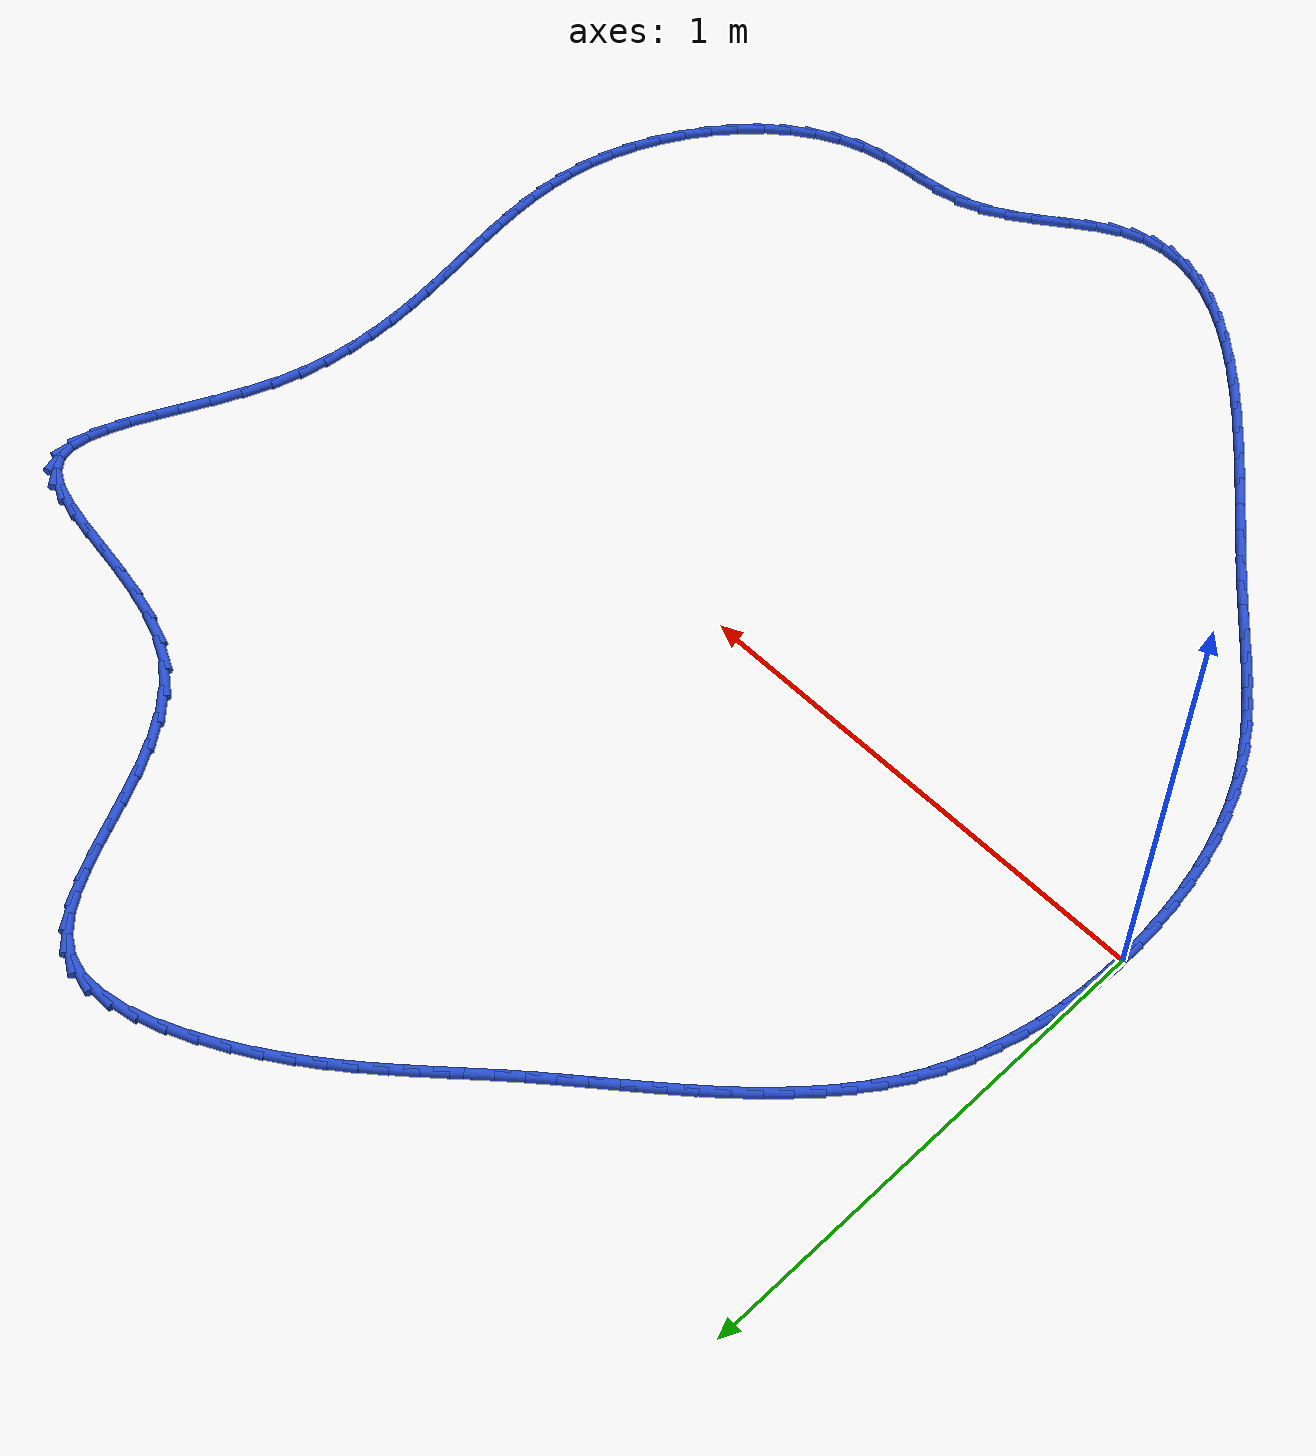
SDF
<sdf version="1.6">
 <world name="default">
  <light name="sun" type="directional">
   <pose>0 0 10 0 -0 0</pose>
   <diffuse>0.8 0.8 0.8 1</diffuse>
   <specular>0.2 0.2 0.2 1</specular>
   <attenuation>
    <range>1000</range>
    <constant>0.9</constant>
    <linear>0.01</linear>
    <quadratic>0.001</quadratic>
   </attenuation>
   <direction>-0.5 0.1 -0.9</direction>
  </light>
  <model name="ground_plane">
   <static>1</static>
   <link name="link">
    <collision name="collision">
     <geometry><plane><normal>0 0 1</normal><size>100 100</size></plane></geometry>
     <surface><friction><ode><mu>100</mu><mu2>50</mu2></ode></friction></surface>
    </collision>
    <visual name="visual">
     <cast_shadows>0</cast_shadows>
     <geometry><plane><normal>0 0 1</normal><size>100 100</size></plane></geometry>
     <material>
      <script><uri>file://media/materials/scripts/gazebo.material</uri><name>Gazebo/WhiteGlow</name></script>
     </material>
    </visual>
   </link>
  </model>
  <gravity>0 0 -9.8</gravity>
  <magnetic_field>6e-06 2.3e-05 -4.2e-05</magnetic_field>
  <atmosphere type="adiabatic"/>
  <physics name="default_physics" default="0" type="ode">
   <max_step_size>0.001</max_step_size>
   <real_time_factor>1</real_time_factor>
   <real_time_update_rate>1000</real_time_update_rate>
  </physics>
  <scene><ambient>0.4 0.4 0.4 1</ambient><background>0.7 0.7 0.7 1</background><shadows>1</shadows></scene>
  <spherical_coordinates>
   <surface_model>EARTH_WGS84</surface_model>
   <latitude_deg>0</latitude_deg>
   <longitude_deg>0</longitude_deg>
   <elevation>0</elevation>
   <heading_deg>0</heading_deg>
  </spherical_coordinates>
  <model name="line">
   <link name="link_0">
    <pose>1.5612511283791264e-17 -6.938893903907228e-17 0.01 0 1.57 1.5524016907554703</pose>
    <collision name="collision">
     <geometry><cylinder><radius>0.01</radius><length>0.08</length></cylinder></geometry>
    </collision>
    <visual name="visual">
     <material>
      <script><name>Gazebo/Blue</name><uri>file://media/materials/scripts/gazebo.material</uri></script>
     </material>
     <geometry><cylinder><radius>0.01</radius><length>0.08</length></cylinder></geometry>
    </visual>
   </link>
   <link name="link_1">
    <pose>0.0010108240448873035 0.0549459109594063 0.01 0 1.57 1.5022052793923284</pose>
    <collision name="collision">
     <geometry><cylinder><radius>0.01</radius><length>0.08</length></cylinder></geometry>
    </collision>
    <visual name="visual">
     <material>
      <script><name>Gazebo/Blue</name><uri>file://media/materials/scripts/gazebo.material</uri></script>
     </material>
     <geometry><cylinder><radius>0.01</radius><length>0.08</length></cylinder></geometry>
    </visual>
   </link>
   <link name="link_2">
    <pose>0.004761709251758233 0.10954488852184022 0.01 0 1.57 1.449477267418357</pose>
    <collision name="collision">
     <geometry><cylinder><radius>0.01</radius><length>0.08</length></cylinder></geometry>
    </collision>
    <visual name="visual">
     <material>
      <script><name>Gazebo/Blue</name><uri>file://media/materials/scripts/gazebo.material</uri></script>
     </material>
     <geometry><cylinder><radius>0.01</radius><length>0.08</length></cylinder></geometry>
    </visual>
   </link>
   <link name="link_3">
    <pose>0.011348165417761865 0.16356863882498898 0.01 0 1.57 1.3938339269967355</pose>
    <collision name="collision">
     <geometry><cylinder><radius>0.01</radius><length>0.08</length></cylinder></geometry>
    </collision>
    <visual name="visual">
     <material>
      <script><name>Gazebo/Blue</name><uri>file://media/materials/scripts/gazebo.material</uri></script>
     </material>
     <geometry><cylinder><radius>0.01</radius><length>0.08</length></cylinder></geometry>
    </visual>
   </link>
   <link name="link_4">
    <pose>0.020865702340047244 0.2167888680065397 0.01 0 1.57 1.3349088024427782</pose>
    <collision name="collision">
     <geometry><cylinder><radius>0.01</radius><length>0.08</length></cylinder></geometry>
    </collision>
    <visual name="visual">
     <material>
      <script><name>Gazebo/Blue</name><uri>file://media/materials/scripts/gazebo.material</uri></script>
     </material>
     <geometry><cylinder><radius>0.01</radius><length>0.08</length></cylinder></geometry>
    </visual>
   </link>
   <link name="link_5">
    <pose>0.03340982981576346 0.2689772822041798 0.01 0 1.57 1.2723695040713148</pose>
    <collision name="collision">
     <geometry><cylinder><radius>0.01</radius><length>0.08</length></cylinder></geometry>
    </collision>
    <visual name="visual">
     <material>
      <script><name>Gazebo/Blue</name><uri>file://media/materials/scripts/gazebo.material</uri></script>
     </material>
     <geometry><cylinder><radius>0.01</radius><length>0.08</length></cylinder></geometry>
    </visual>
   </link>
   <link name="link_6">
    <pose>0.049076057642059565 0.3199055875555965 0.01 0 1.57 1.205941755668976</pose>
    <collision name="collision">
     <geometry><cylinder><radius>0.01</radius><length>0.08</length></cylinder></geometry>
    </collision>
    <visual name="visual">
     <material>
      <script><name>Gazebo/Blue</name><uri>file://media/materials/scripts/gazebo.material</uri></script>
     </material>
     <geometry><cylinder><radius>0.01</radius><length>0.08</length></cylinder></geometry>
    </visual>
   </link>
   <link name="link_7">
    <pose>0.06795989561608459 0.3693454901984769 0.01 0 1.57 1.1354410207944292</pose>
    <collision name="collision">
     <geometry><cylinder><radius>0.01</radius><length>0.08</length></cylinder></geometry>
    </collision>
    <visual name="visual">
     <material>
      <script><name>Gazebo/Blue</name><uri>file://media/materials/scripts/gazebo.material</uri></script>
     </material>
     <geometry><cylinder><radius>0.01</radius><length>0.08</length></cylinder></geometry>
    </visual>
   </link>
   <link name="link_8">
    <pose>0.09015685353498762 0.41706869627050835 0.01 0 1.57 1.0613098449842502</pose>
    <collision name="collision">
     <geometry><cylinder><radius>0.01</radius><length>0.08</length></cylinder></geometry>
    </collision>
    <visual name="visual">
     <material>
      <script><name>Gazebo/Blue</name><uri>file://media/materials/scripts/gazebo.material</uri></script>
     </material>
     <geometry><cylinder><radius>0.01</radius><length>0.08</length></cylinder></geometry>
    </visual>
   </link>
   <link name="link_9">
    <pose>0.11574240478994677 0.46286474245704146 0.01 0 1.57 0.9902246973115312</pose>
    <collision name="collision">
     <geometry><cylinder><radius>0.01</radius><length>0.08</length></cylinder></geometry>
    </collision>
    <visual name="visual">
     <material>
      <script><name>Gazebo/Blue</name><uri>file://media/materials/scripts/gazebo.material</uri></script>
     </material>
     <geometry><cylinder><radius>0.01</radius><length>0.08</length></cylinder></geometry>
    </visual>
   </link>
   <link name="link_10">
    <pose>0.1445329476938466 0.506753718294999 0.01 0 1.57 0.9271506494640671</pose>
    <collision name="collision">
     <geometry><cylinder><radius>0.01</radius><length>0.08</length></cylinder></geometry>
    </collision>
    <visual name="visual">
     <material>
      <script><name>Gazebo/Blue</name><uri>file://media/materials/scripts/gazebo.material</uri></script>
     </material>
     <geometry><cylinder><radius>0.01</radius><length>0.08</length></cylinder></geometry>
    </visual>
   </link>
   <link name="link_11">
    <pose>0.1761644163634784 0.5489163097603373 0.01 0 1.57 0.8723713835519302</pose>
    <collision name="collision">
     <geometry><cylinder><radius>0.01</radius><length>0.08</length></cylinder></geometry>
    </collision>
    <visual name="visual">
     <material>
      <script><name>Gazebo/Blue</name><uri>file://media/materials/scripts/gazebo.material</uri></script>
     </material>
     <geometry><cylinder><radius>0.01</radius><length>0.08</length></cylinder></geometry>
    </visual>
   </link>
   <link name="link_12">
    <pose>0.21026907791694047 0.5895364661185993 0.01 0 1.57 0.8258091247689291</pose>
    <collision name="collision">
     <geometry><cylinder><radius>0.01</radius><length>0.08</length></cylinder></geometry>
    </collision>
    <visual name="visual">
     <material>
      <script><name>Gazebo/Blue</name><uri>file://media/materials/scripts/gazebo.material</uri></script>
     </material>
     <geometry><cylinder><radius>0.01</radius><length>0.08</length></cylinder></geometry>
    </visual>
   </link>
   <link name="link_13">
    <pose>0.24647919947233096 0.6287981366353289 0.01 0 1.57 0.7872300190082603</pose>
    <collision name="collision">
     <geometry><cylinder><radius>0.01</radius><length>0.08</length></cylinder></geometry>
    </collision>
    <visual name="visual">
     <material>
      <script><name>Gazebo/Blue</name><uri>file://media/materials/scripts/gazebo.material</uri></script>
     </material>
     <geometry><cylinder><radius>0.01</radius><length>0.08</length></cylinder></geometry>
    </visual>
   </link>
   <link name="link_14">
    <pose>0.2844270481477484 0.6668852705760694 0.01 0 1.57 0.7563372634830966</pose>
    <collision name="collision">
     <geometry><cylinder><radius>0.01</radius><length>0.08</length></cylinder></geometry>
    </collision>
    <visual name="visual">
     <material>
      <script><name>Gazebo/Blue</name><uri>file://media/materials/scripts/gazebo.material</uri></script>
     </material>
     <geometry><cylinder><radius>0.01</radius><length>0.08</length></cylinder></geometry>
    </visual>
   </link>
   <link name="link_15">
    <pose>0.32374489106129073 0.703981817206364 0.01 0 1.57 0.7328399677386845</pose>
    <collision name="collision">
     <geometry><cylinder><radius>0.01</radius><length>0.08</length></cylinder></geometry>
    </collision>
    <visual name="visual">
     <material>
      <script><name>Gazebo/Blue</name><uri>file://media/materials/scripts/gazebo.material</uri></script>
     </material>
     <geometry><cylinder><radius>0.01</radius><length>0.08</length></cylinder></geometry>
    </visual>
   </link>
   <link name="link_16">
    <pose>0.3640649953310566 0.7402717257917565 0.01 0 1.57 0.716500793619048</pose>
    <collision name="collision">
     <geometry><cylinder><radius>0.01</radius><length>0.08</length></cylinder></geometry>
    </collision>
    <visual name="visual">
     <material>
      <script><name>Gazebo/Blue</name><uri>file://media/materials/scripts/gazebo.material</uri></script>
     </material>
     <geometry><cylinder><radius>0.01</radius><length>0.08</length></cylinder></geometry>
    </visual>
   </link>
   <link name="link_17">
    <pose>0.4050196280751439 0.7759389455977901 0.01 0 1.57 0.7071676263991836</pose>
    <collision name="collision">
     <geometry><cylinder><radius>0.01</radius><length>0.08</length></cylinder></geometry>
    </collision>
    <visual name="visual">
     <material>
      <script><name>Gazebo/Blue</name><uri>file://media/materials/scripts/gazebo.material</uri></script>
     </material>
     <geometry><cylinder><radius>0.01</radius><length>0.08</length></cylinder></geometry>
    </visual>
   </link>
   <link name="link_18">
    <pose>0.446241056411651 0.8111674258900079 0.01 0 1.57 0.7047943213423088</pose>
    <collision name="collision">
     <geometry><cylinder><radius>0.01</radius><length>0.08</length></cylinder></geometry>
    </collision>
    <visual name="visual">
     <material>
      <script><name>Gazebo/Blue</name><uri>file://media/materials/scripts/gazebo.material</uri></script>
     </material>
     <geometry><cylinder><radius>0.01</radius><length>0.08</length></cylinder></geometry>
    </visual>
   </link>
   <link name="link_19">
    <pose>0.48736154745867655 0.8461411159339542 0.01 0 1.57 0.7094542777418011</pose>
    <collision name="collision">
     <geometry><cylinder><radius>0.01</radius><length>0.08</length></cylinder></geometry>
    </collision>
    <visual name="visual">
     <material>
      <script><name>Gazebo/Blue</name><uri>file://media/materials/scripts/gazebo.material</uri></script>
     </material>
     <geometry><cylinder><radius>0.01</radius><length>0.08</length></cylinder></geometry>
    </visual>
   </link>
   <link name="link_20">
    <pose>0.5280133683343184 0.8810439649951719 0.01 0 1.57 0.7213397730226309</pose>
    <collision name="collision">
     <geometry><cylinder><radius>0.01</radius><length>0.08</length></cylinder></geometry>
    </collision>
    <visual name="visual">
     <material>
      <script><name>Gazebo/Blue</name><uri>file://media/materials/scripts/gazebo.material</uri></script>
     </material>
     <geometry><cylinder><radius>0.01</radius><length>0.08</length></cylinder></geometry>
    </visual>
   </link>
   <link name="link_21">
    <pose>0.5678292780076015 0.9160597116324382 0.01 0 1.57 0.7368221955592761</pose>
    <collision name="collision">
     <geometry><cylinder><radius>0.01</radius><length>0.08</length></cylinder></geometry>
    </collision>
    <visual name="visual">
     <material>
      <script><name>Gazebo/Blue</name><uri>file://media/materials/scripts/gazebo.material</uri></script>
     </material>
     <geometry><cylinder><radius>0.01</radius><length>0.08</length></cylinder></geometry>
    </visual>
   </link>
   <link name="link_22">
    <pose>0.6066515428900895 0.9512823423407987 0.01 0 1.57 0.7458170189217816</pose>
    <collision name="collision">
     <geometry><cylinder><radius>0.01</radius><length>0.08</length></cylinder></geometry>
    </collision>
    <visual name="visual">
     <material>
      <script><name>Gazebo/Blue</name><uri>file://media/materials/scripts/gazebo.material</uri></script>
     </material>
     <geometry><cylinder><radius>0.01</radius><length>0.08</length></cylinder></geometry>
    </visual>
   </link>
   <link name="link_23">
    <pose>0.6448568355704528 0.9865769063676033 0.01 0 1.57 0.7464607491922605</pose>
    <collision name="collision">
     <geometry><cylinder><radius>0.01</radius><length>0.08</length></cylinder></geometry>
    </collision>
    <visual name="visual">
     <material>
      <script><name>Gazebo/Blue</name><uri>file://media/materials/scripts/gazebo.material</uri></script>
     </material>
     <geometry><cylinder><radius>0.01</radius><length>0.08</length></cylinder></geometry>
    </visual>
   </link>
   <link name="link_24">
    <pose>0.682905803055435 1.0217724786901177 0.01 0 1.57 0.7386570811903604</pose>
    <collision name="collision">
     <geometry><cylinder><radius>0.01</radius><length>0.08</length></cylinder></geometry>
    </collision>
    <visual name="visual">
     <material>
      <script><name>Gazebo/Blue</name><uri>file://media/materials/scripts/gazebo.material</uri></script>
     </material>
     <geometry><cylinder><radius>0.01</radius><length>0.08</length></cylinder></geometry>
    </visual>
   </link>
   <link name="link_25">
    <pose>0.7212590923517799 1.0566981342856065 0.01 0 1.57 0.7225293456745581</pose>
    <collision name="collision">
     <geometry><cylinder><radius>0.01</radius><length>0.08</length></cylinder></geometry>
    </collision>
    <visual name="visual">
     <material>
      <script><name>Gazebo/Blue</name><uri>file://media/materials/scripts/gazebo.material</uri></script>
     </material>
     <geometry><cylinder><radius>0.01</radius><length>0.08</length></cylinder></geometry>
    </visual>
   </link>
   <link name="link_26">
    <pose>0.7603773504662302 1.0911829481313353 0.01 0 1.57 0.6984300620595036</pose>
    <collision name="collision">
     <geometry><cylinder><radius>0.01</radius><length>0.08</length></cylinder></geometry>
    </collision>
    <visual name="visual">
     <material>
      <script><name>Gazebo/Blue</name><uri>file://media/materials/scripts/gazebo.material</uri></script>
     </material>
     <geometry><cylinder><radius>0.01</radius><length>0.08</length></cylinder></geometry>
    </visual>
   </link>
   <link name="link_27">
    <pose>0.8007212244055302 1.1250559952045691 0.01 0 1.57 0.6669493440624943</pose>
    <collision name="collision">
     <geometry><cylinder><radius>0.01</radius><length>0.08</length></cylinder></geometry>
    </collision>
    <visual name="visual">
     <material>
      <script><name>Gazebo/Blue</name><uri>file://media/materials/scripts/gazebo.material</uri></script>
     </material>
     <geometry><cylinder><radius>0.01</radius><length>0.08</length></cylinder></geometry>
    </visual>
   </link>
   <link name="link_28">
    <pose>0.8427513611764228 1.158146350482573 0.01 0 1.57 0.6289143823704977</pose>
    <collision name="collision">
     <geometry><cylinder><radius>0.01</radius><length>0.08</length></cylinder></geometry>
    </collision>
    <visual name="visual">
     <material>
      <script><name>Gazebo/Blue</name><uri>file://media/materials/scripts/gazebo.material</uri></script>
     </material>
     <geometry><cylinder><radius>0.01</radius><length>0.08</length></cylinder></geometry>
    </visual>
   </link>
   <link name="link_29">
    <pose>0.8869284077856517 1.1902830889426124 0.01 0 1.57 0.5853708190399936</pose>
    <collision name="collision">
     <geometry><cylinder><radius>0.01</radius><length>0.08</length></cylinder></geometry>
    </collision>
    <visual name="visual">
     <material>
      <script><name>Gazebo/Blue</name><uri>file://media/materials/scripts/gazebo.material</uri></script>
     </material>
     <geometry><cylinder><radius>0.01</radius><length>0.08</length></cylinder></geometry>
    </visual>
   </link>
   <link name="link_30">
    <pose>0.9337130112399603 1.2212952855619525 0.01 0 1.57 0.537498812886988</pose>
    <collision name="collision">
     <geometry><cylinder><radius>0.01</radius><length>0.08</length></cylinder></geometry>
    </collision>
    <visual name="visual">
     <material>
      <script><name>Gazebo/Blue</name><uri>file://media/materials/scripts/gazebo.material</uri></script>
     </material>
     <geometry><cylinder><radius>0.01</radius><length>0.08</length></cylinder></geometry>
    </visual>
   </link>
   <link name="link_31">
    <pose>0.9835530021196068 1.2510016546847316 0.01 0 1.57 0.4833694559610374</pose>
    <collision name="collision">
     <geometry><cylinder><radius>0.01</radius><length>0.08</length></cylinder></geometry>
    </collision>
    <visual name="visual">
     <material>
      <script><name>Gazebo/Blue</name><uri>file://media/materials/scripts/gazebo.material</uri></script>
     </material>
     <geometry><cylinder><radius>0.01</radius><length>0.08</length></cylinder></geometry>
    </visual>
   </link>
   <link name="link_32">
    <pose>1.0361224592673037 1.2785954197748408 0.01 0 1.57 0.415183490230197</pose>
    <collision name="collision">
     <geometry><cylinder><radius>0.01</radius><length>0.08</length></cylinder></geometry>
    </collision>
    <visual name="visual">
     <material>
      <script><name>Gazebo/Blue</name><uri>file://media/materials/scripts/gazebo.material</uri></script>
     </material>
     <geometry><cylinder><radius>0.01</radius><length>0.08</length></cylinder></geometry>
    </visual>
   </link>
   <link name="link_33">
    <pose>1.0898933977398046 1.3022980715050083 0.01 0 1.57 0.3245983488699011</pose>
    <collision name="collision">
     <geometry><cylinder><radius>0.01</radius><length>0.08</length></cylinder></geometry>
    </collision>
    <visual name="visual">
     <material>
      <script><name>Gazebo/Blue</name><uri>file://media/materials/scripts/gazebo.material</uri></script>
     </material>
     <geometry><cylinder><radius>0.01</radius><length>0.08</length></cylinder></geometry>
    </visual>
   </link>
   <link name="link_34">
    <pose>1.1432341073414867 1.3202472503977598 0.01 0 1.57 0.1988500874779073</pose>
    <collision name="collision">
     <geometry><cylinder><radius>0.01</radius><length>0.08</length></cylinder></geometry>
    </collision>
    <visual name="visual">
     <material>
      <script><name>Gazebo/Blue</name><uri>file://media/materials/scripts/gazebo.material</uri></script>
     </material>
     <geometry><cylinder><radius>0.01</radius><length>0.08</length></cylinder></geometry>
    </visual>
   </link>
   <link name="link_35">
    <pose>1.1945128778767262 1.3305805969756195 0.01 0 1.57 0.017969119769651622</pose>
    <collision name="collision">
     <geometry><cylinder><radius>0.01</radius><length>0.08</length></cylinder></geometry>
    </collision>
    <visual name="visual">
     <material>
      <script><name>Gazebo/Blue</name><uri>file://media/materials/scripts/gazebo.material</uri></script>
     </material>
     <geometry><cylinder><radius>0.01</radius><length>0.08</length></cylinder></geometry>
    </visual>
   </link>
   <link name="link_36">
    <pose>1.2420979991498984 1.331435751761112 0.01 0 1.57 -0.2406301265532608</pose>
    <collision name="collision">
     <geometry><cylinder><radius>0.01</radius><length>0.08</length></cylinder></geometry>
    </collision>
    <visual name="visual">
     <material>
      <script><name>Gazebo/Blue</name><uri>file://media/materials/scripts/gazebo.material</uri></script>
     </material>
     <geometry><cylinder><radius>0.01</radius><length>0.08</length></cylinder></geometry>
    </visual>
   </link>
   <link name="link_37">
    <pose>1.2844319771622554 1.3210476426094253 0.01 0 1.57 -0.5293358232400482</pose>
    <collision name="collision">
     <geometry><cylinder><radius>0.01</radius><length>0.08</length></cylinder></geometry>
    </collision>
    <visual name="visual">
     <material>
      <script><name>Gazebo/Blue</name><uri>file://media/materials/scripts/gazebo.material</uri></script>
     </material>
     <geometry><cylinder><radius>0.01</radius><length>0.08</length></cylinder></geometry>
    </visual>
   </link>
   <link name="link_38">
    <pose>1.3213356826673583 1.299458045959166 0.01 0 1.57 -0.7640713369873696</pose>
    <collision name="collision">
     <geometry><cylinder><radius>0.01</radius><length>0.08</length></cylinder></geometry>
    </collision>
    <visual name="visual">
     <material>
      <script><name>Gazebo/Blue</name><uri>file://media/materials/scripts/gazebo.material</uri></script>
     </material>
     <geometry><cylinder><radius>0.01</radius><length>0.08</length></cylinder></geometry>
    </visual>
   </link>
   <link name="link_39">
    <pose>1.3538472742662049 1.268304436933968 0.01 0 1.57 -0.9284357862294297</pose>
    <collision name="collision">
     <geometry><cylinder><radius>0.01</radius><length>0.08</length></cylinder></geometry>
    </collision>
    <visual name="visual">
     <material>
      <script><name>Gazebo/Blue</name><uri>file://media/materials/scripts/gazebo.material</uri></script>
     </material>
     <geometry><cylinder><radius>0.01</radius><length>0.08</length></cylinder></geometry>
    </visual>
   </link>
   <link name="link_40">
    <pose>1.3830467553323234 1.229279143458835 0.01 0 1.57 -1.0329086433006016</pose>
    <collision name="collision">
     <geometry><cylinder><radius>0.01</radius><length>0.08</length></cylinder></geometry>
    </collision>
    <visual name="visual">
     <material>
      <script><name>Gazebo/Blue</name><uri>file://media/materials/scripts/gazebo.material</uri></script>
     </material>
     <geometry><cylinder><radius>0.01</radius><length>0.08</length></cylinder></geometry>
    </visual>
   </link>
   <link name="link_41">
    <pose>1.4100141292392454 1.1840744934587717 0.01 0 1.57 -1.0916636704700757</pose>
    <collision name="collision">
     <geometry><cylinder><radius>0.01</radius><length>0.08</length></cylinder></geometry>
    </collision>
    <visual name="visual">
     <material>
      <script><name>Gazebo/Blue</name><uri>file://media/materials/scripts/gazebo.material</uri></script>
     </material>
     <geometry><cylinder><radius>0.01</radius><length>0.08</length></cylinder></geometry>
    </visual>
   </link>
   <link name="link_42">
    <pose>1.4358293993605002 1.1343828148587827 0.01 0 1.57 -1.1147990505419347</pose>
    <collision name="collision">
     <geometry><cylinder><radius>0.01</radius><length>0.08</length></cylinder></geometry>
    </collision>
    <visual name="visual">
     <material>
      <script><name>Gazebo/Blue</name><uri>file://media/materials/scripts/gazebo.material</uri></script>
     </material>
     <geometry><cylinder><radius>0.01</radius><length>0.08</length></cylinder></geometry>
    </visual>
   </link>
   <link name="link_43">
    <pose>1.461572569069618 1.0818964355838723 0.01 0 1.57 -1.107795380917502</pose>
    <collision name="collision">
     <geometry><cylinder><radius>0.01</radius><length>0.08</length></cylinder></geometry>
    </collision>
    <visual name="visual">
     <material>
      <script><name>Gazebo/Blue</name><uri>file://media/materials/scripts/gazebo.material</uri></script>
     </material>
     <geometry><cylinder><radius>0.01</radius><length>0.08</length></cylinder></geometry>
    </visual>
   </link>
   <link name="link_44">
    <pose>1.488323641740128 1.0283076835590441 0.01 0 1.57 -1.0724601751161738</pose>
    <collision name="collision">
     <geometry><cylinder><radius>0.01</radius><length>0.08</length></cylinder></geometry>
    </collision>
    <visual name="visual">
     <material>
      <script><name>Gazebo/Blue</name><uri>file://media/materials/scripts/gazebo.material</uri></script>
     </material>
     <geometry><cylinder><radius>0.01</radius><length>0.08</length></cylinder></geometry>
    </visual>
   </link>
   <link name="link_45">
    <pose>1.5171626207455606 0.9753088867093035 0.01 0 1.57 -1.0078267898354718</pose>
    <collision name="collision">
     <geometry><cylinder><radius>0.01</radius><length>0.08</length></cylinder></geometry>
    </collision>
    <visual name="visual">
     <material>
      <script><name>Gazebo/Blue</name><uri>file://media/materials/scripts/gazebo.material</uri></script>
     </material>
     <geometry><cylinder><radius>0.01</radius><length>0.08</length></cylinder></geometry>
    </visual>
   </link>
   <link name="link_46">
    <pose>1.5491695094594462 0.9245923729596535 0.01 0 1.57 -0.9110877091274001</pose>
    <collision name="collision">
     <geometry><cylinder><radius>0.01</radius><length>0.08</length></cylinder></geometry>
    </collision>
    <visual name="visual">
     <material>
      <script><name>Gazebo/Blue</name><uri>file://media/materials/scripts/gazebo.material</uri></script>
     </material>
     <geometry><cylinder><radius>0.01</radius><length>0.08</length></cylinder></geometry>
    </visual>
   </link>
   <link name="link_47">
    <pose>1.5854243112553137 0.8778504702350994 0.01 0 1.57 -0.7792553817712297</pose>
    <collision name="collision">
     <geometry><cylinder><radius>0.01</radius><length>0.08</length></cylinder></geometry>
    </collision>
    <visual name="visual">
     <material>
      <script><name>Gazebo/Blue</name><uri>file://media/materials/scripts/gazebo.material</uri></script>
     </material>
     <geometry><cylinder><radius>0.01</radius><length>0.08</length></cylinder></geometry>
    </visual>
   </link>
   <link name="link_48">
    <pose>1.6270070295066943 0.8367755064606452 0.01 0 1.57 -0.6124872750445732</pose>
    <collision name="collision">
     <geometry><cylinder><radius>0.01</radius><length>0.08</length></cylinder></geometry>
    </collision>
    <visual name="visual">
     <material>
      <script><name>Gazebo/Blue</name><uri>file://media/materials/scripts/gazebo.material</uri></script>
     </material>
     <geometry><cylinder><radius>0.01</radius><length>0.08</length></cylinder></geometry>
    </visual>
   </link>
   <link name="link_49">
    <pose>1.6749954733802017 0.8030575015443351 0.01 0 1.57 -0.4372053470558105</pose>
    <collision name="collision">
     <geometry><cylinder><radius>0.01</radius><length>0.08</length></cylinder></geometry>
    </collision>
    <visual name="visual">
     <material>
      <script><name>Gazebo/Blue</name><uri>file://media/materials/scripts/gazebo.material</uri></script>
     </material>
     <geometry><cylinder><radius>0.01</radius><length>0.08</length></cylinder></geometry>
    </visual>
   </link>
   <link name="link_50">
    <pose>1.7296414032931275 0.7775175808015371 0.01 0 1.57 -0.30471559002188786</pose>
    <collision name="collision">
     <geometry><cylinder><radius>0.01</radius><length>0.08</length></cylinder></geometry>
    </collision>
    <visual name="visual">
     <material>
      <script><name>Gazebo/Blue</name><uri>file://media/materials/scripts/gazebo.material</uri></script>
     </material>
     <geometry><cylinder><radius>0.01</radius><length>0.08</length></cylinder></geometry>
    </visual>
   </link>
   <link name="link_51">
    <pose>1.7891334277363482 0.758806705190862 0.01 0 1.57 -0.21467783498044857</pose>
    <collision name="collision">
     <geometry><cylinder><radius>0.01</radius><length>0.08</length></cylinder></geometry>
    </collision>
    <visual name="visual">
     <material>
      <script><name>Gazebo/Blue</name><uri>file://media/materials/scripts/gazebo.material</uri></script>
     </material>
     <geometry><cylinder><radius>0.01</radius><length>0.08</length></cylinder></geometry>
    </visual>
   </link>
   <link name="link_52">
    <pose>1.8513433484317807 0.7452425966354532 0.01 0 1.57 -0.15945756182556056</pose>
    <collision name="collision">
     <geometry><cylinder><radius>0.01</radius><length>0.08</length></cylinder></geometry>
    </collision>
    <visual name="visual">
     <material>
      <script><name>Gazebo/Blue</name><uri>file://media/materials/scripts/gazebo.material</uri></script>
     </material>
     <geometry><cylinder><radius>0.01</radius><length>0.08</length></cylinder></geometry>
    </visual>
   </link>
   <link name="link_53">
    <pose>1.9141429671013397 0.7351429770584544 0.01 0 1.57 -0.13494465432601432</pose>
    <collision name="collision">
     <geometry><cylinder><radius>0.01</radius><length>0.08</length></cylinder></geometry>
    </collision>
    <visual name="visual">
     <material>
      <script><name>Gazebo/Blue</name><uri>file://media/materials/scripts/gazebo.material</uri></script>
     </material>
     <geometry><cylinder><radius>0.01</radius><length>0.08</length></cylinder></geometry>
    </visual>
   </link>
   <link name="link_54">
    <pose>1.975404085466942 0.7268255683830094 0.01 0 1.57 -0.1417218173406719</pose>
    <collision name="collision">
     <geometry><cylinder><radius>0.01</radius><length>0.08</length></cylinder></geometry>
    </collision>
    <visual name="visual">
     <material>
      <script><name>Gazebo/Blue</name><uri>file://media/materials/scripts/gazebo.material</uri></script>
     </material>
     <geometry><cylinder><radius>0.01</radius><length>0.08</length></cylinder></geometry>
    </visual>
   </link>
   <link name="link_55">
    <pose>2.0329985052505033 0.7186080925322614 0.01 0 1.57 -0.18697761784973563</pose>
    <collision name="collision">
     <geometry><cylinder><radius>0.01</radius><length>0.08</length></cylinder></geometry>
    </collision>
    <visual name="visual">
     <material>
      <script><name>Gazebo/Blue</name><uri>file://media/materials/scripts/gazebo.material</uri></script>
     </material>
     <geometry><cylinder><radius>0.01</radius><length>0.08</length></cylinder></geometry>
    </visual>
   </link>
   <link name="link_56">
    <pose>2.0847980281739398 0.7088082714293544 0.01 0 1.57 -0.2893962819560187</pose>
    <collision name="collision">
     <geometry><cylinder><radius>0.01</radius><length>0.08</length></cylinder></geometry>
    </collision>
    <visual name="visual">
     <material>
      <script><name>Gazebo/Blue</name><uri>file://media/materials/scripts/gazebo.material</uri></script>
     </material>
     <geometry><cylinder><radius>0.01</radius><length>0.08</length></cylinder></geometry>
    </visual>
   </link>
   <link name="link_57">
    <pose>2.1286744559591684 0.6957438269974323 0.01 0 1.57 -0.4892959162293456</pose>
    <collision name="collision">
     <geometry><cylinder><radius>0.01</radius><length>0.08</length></cylinder></geometry>
    </collision>
    <visual name="visual">
     <material>
      <script><name>Gazebo/Blue</name><uri>file://media/materials/scripts/gazebo.material</uri></script>
     </material>
     <geometry><cylinder><radius>0.01</radius><length>0.08</length></cylinder></geometry>
    </visual>
   </link>
   <link name="link_58">
    <pose>2.162499590328103 0.6777324811596384 0.01 0 1.57 -0.8500113142360899</pose>
    <collision name="collision">
     <geometry><cylinder><radius>0.01</radius><length>0.08</length></cylinder></geometry>
    </collision>
    <visual name="visual">
     <material>
      <script><name>Gazebo/Blue</name><uri>file://media/materials/scripts/gazebo.material</uri></script>
     </material>
     <geometry><cylinder><radius>0.01</radius><length>0.08</length></cylinder></geometry>
    </visual>
   </link>
   <link name="link_59">
    <pose>2.184145244329629 0.6530919628522066 0.01 0 1.57 -1.3249582075143458</pose>
    <collision name="collision">
     <geometry><cylinder><radius>0.01</radius><length>0.08</length></cylinder></geometry>
    </collision>
    <visual name="visual">
     <material>
      <script><name>Gazebo/Blue</name><uri>file://media/materials/scripts/gazebo.material</uri></script>
     </material>
     <geometry><cylinder><radius>0.01</radius><length>0.08</length></cylinder></geometry>
    </visual>
   </link>
   <link name="link_60">
    <pose>2.1922882672988475 0.6206384390985227 0.01 0 1.57 1.4778109682365663</pose>
    <collision name="collision">
     <geometry><cylinder><radius>0.01</radius><length>0.08</length></cylinder></geometry>
    </collision>
    <visual name="visual">
     <material>
      <script><name>Gazebo/Blue</name><uri>file://media/materials/scripts/gazebo.material</uri></script>
     </material>
     <geometry><cylinder><radius>0.01</radius><length>0.08</length></cylinder></geometry>
    </visual>
   </link>
   <link name="link_61">
    <pose>2.1885954796398344 0.5810393170285 0.01 0 1.57 1.2899548030121113</pose>
    <collision name="collision">
     <geometry><cylinder><radius>0.01</radius><length>0.08</length></cylinder></geometry>
    </collision>
    <visual name="visual">
     <material>
      <script><name>Gazebo/Blue</name><uri>file://media/materials/scripts/gazebo.material</uri></script>
     </material>
     <geometry><cylinder><radius>0.01</radius><length>0.08</length></cylinder></geometry>
    </visual>
   </link>
   <link name="link_62">
    <pose>2.1754277095418684 0.5353916985806557 0.01 0 1.57 1.1895691542380549</pose>
    <collision name="collision">
     <geometry><cylinder><radius>0.01</radius><length>0.08</length></cylinder></geometry>
    </collision>
    <visual name="visual">
     <material>
      <script><name>Gazebo/Blue</name><uri>file://media/materials/scripts/gazebo.material</uri></script>
     </material>
     <geometry><cylinder><radius>0.01</radius><length>0.08</length></cylinder></geometry>
    </visual>
   </link>
   <link name="link_63">
    <pose>2.155145785194225 0.4847926856935044 0.01 0 1.57 1.1398587406413696</pose>
    <collision name="collision">
     <geometry><cylinder><radius>0.01</radius><length>0.08</length></cylinder></geometry>
    </collision>
    <visual name="visual">
     <material>
      <script><name>Gazebo/Blue</name><uri>file://media/materials/scripts/gazebo.material</uri></script>
     </material>
     <geometry><cylinder><radius>0.01</radius><length>0.08</length></cylinder></geometry>
    </visual>
   </link>
   <link name="link_64">
    <pose>2.1301105347861826 0.4303393803055638 0.01 0 1.57 1.1237493802541416</pose>
    <collision name="collision">
     <geometry><cylinder><radius>0.01</radius><length>0.08</length></cylinder></geometry>
    </collision>
    <visual name="visual">
     <material>
      <script><name>Gazebo/Blue</name><uri>file://media/materials/scripts/gazebo.material</uri></script>
     </material>
     <geometry><cylinder><radius>0.01</radius><length>0.08</length></cylinder></geometry>
    </visual>
   </link>
   <link name="link_65">
    <pose>2.1026827865070197 0.3731288843553489 0.01 0 1.57 1.134357790968661</pose>
    <collision name="collision">
     <geometry><cylinder><radius>0.01</radius><length>0.08</length></cylinder></geometry>
    </collision>
    <visual name="visual">
     <material>
      <script><name>Gazebo/Blue</name><uri>file://media/materials/scripts/gazebo.material</uri></script>
     </material>
     <geometry><cylinder><radius>0.01</radius><length>0.08</length></cylinder></geometry>
    </visual>
   </link>
   <link name="link_66">
    <pose>2.075223368546012 0.3142582997813757 0.01 0 1.57 1.1707656587022828</pose>
    <collision name="collision">
     <geometry><cylinder><radius>0.01</radius><length>0.08</length></cylinder></geometry>
    </collision>
    <visual name="visual">
     <material>
      <script><name>Gazebo/Blue</name><uri>file://media/materials/scripts/gazebo.material</uri></script>
     </material>
     <geometry><cylinder><radius>0.01</radius><length>0.08</length></cylinder></geometry>
    </visual>
   </link>
   <link name="link_67">
    <pose>2.0500931090924386 0.2548247285221609 0.01 0 1.57 1.236489933139924</pose>
    <collision name="collision">
     <geometry><cylinder><radius>0.01</radius><length>0.08</length></cylinder></geometry>
    </collision>
    <visual name="visual">
     <material>
      <script><name>Gazebo/Blue</name><uri>file://media/materials/scripts/gazebo.material</uri></script>
     </material>
     <geometry><cylinder><radius>0.01</radius><length>0.08</length></cylinder></geometry>
    </visual>
   </link>
   <link name="link_68">
    <pose>2.029631904074261 0.1959170569464824 0.01 0 1.57 1.3229887396434812</pose>
    <collision name="collision">
     <geometry><cylinder><radius>0.01</radius><length>0.08</length></cylinder></geometry>
    </collision>
    <visual name="visual">
     <material>
      <script><name>Gazebo/Blue</name><uri>file://media/materials/scripts/gazebo.material</uri></script>
     </material>
     <geometry><cylinder><radius>0.01</radius><length>0.08</length></cylinder></geometry>
    </visual>
   </link>
   <link name="link_69">
    <pose>2.015021330576708 0.13816955024829486 0.01 0 1.57 1.4077039055124525</pose>
    <collision name="collision">
     <geometry><cylinder><radius>0.01</radius><length>0.08</length></cylinder></geometry>
    </collision>
    <visual name="visual">
     <material>
      <script><name>Gazebo/Blue</name><uri>file://media/materials/scripts/gazebo.material</uri></script>
     </material>
     <geometry><cylinder><radius>0.01</radius><length>0.08</length></cylinder></geometry>
    </visual>
   </link>
   <link name="link_70">
    <pose>2.0057015589291085 0.08153299999062318 0.01 0 1.57 1.4859321556896317</pose>
    <collision name="collision">
     <geometry><cylinder><radius>0.01</radius><length>0.08</length></cylinder></geometry>
    </collision>
    <visual name="visual">
     <material>
      <script><name>Gazebo/Blue</name><uri>file://media/materials/scripts/gazebo.material</uri></script>
     </material>
     <geometry><cylinder><radius>0.01</radius><length>0.08</length></cylinder></geometry>
    </visual>
   </link>
   <link name="link_71">
    <pose>2.0009690979474333 0.025901812945391893 0.01 0 1.57 1.555292005066923</pose>
    <collision name="collision">
     <geometry><cylinder><radius>0.01</radius><length>0.08</length></cylinder></geometry>
    </collision>
    <visual name="visual">
     <material>
      <script><name>Gazebo/Blue</name><uri>file://media/materials/scripts/gazebo.material</uri></script>
     </material>
     <geometry><cylinder><radius>0.01</radius><length>0.08</length></cylinder></geometry>
    </visual>
   </link>
   <link name="link_72">
    <pose>2.00012045644766 -0.028829604115475915 0.01 0 1.57 -1.527593598485886</pose>
    <collision name="collision">
     <geometry><cylinder><radius>0.01</radius><length>0.08</length></cylinder></geometry>
    </collision>
    <visual name="visual">
     <material>
      <script><name>Gazebo/Blue</name><uri>file://media/materials/scripts/gazebo.material</uri></script>
     </material>
     <geometry><cylinder><radius>0.01</radius><length>0.08</length></cylinder></geometry>
    </visual>
   </link>
   <link name="link_73">
    <pose>2.0024521432457614 -0.08276684442005745 0.01 0 1.57 -1.4807374004935128</pose>
    <collision name="collision">
     <geometry><cylinder><radius>0.01</radius><length>0.08</length></cylinder></geometry>
    </collision>
    <visual name="visual">
     <material>
      <script><name>Gazebo/Blue</name><uri>file://media/materials/scripts/gazebo.material</uri></script>
     </material>
     <geometry><cylinder><radius>0.01</radius><length>0.08</length></cylinder></geometry>
    </visual>
   </link>
   <link name="link_74">
    <pose>2.0072606671577127 -0.1360155011964274 0.01 0 1.57 -1.446466355762532</pose>
    <collision name="collision">
     <geometry><cylinder><radius>0.01</radius><length>0.08</length></cylinder></geometry>
    </collision>
    <visual name="visual">
     <material>
      <script><name>Gazebo/Blue</name><uri>file://media/materials/scripts/gazebo.material</uri></script>
     </material>
     <geometry><cylinder><radius>0.01</radius><length>0.08</length></cylinder></geometry>
    </visual>
   </link>
   <link name="link_75">
    <pose>2.0138425369994892 -0.18868116767266307 0.01 0 1.57 -1.425215871566464</pose>
    <collision name="collision">
     <geometry><cylinder><radius>0.01</radius><length>0.08</length></cylinder></geometry>
    </collision>
    <visual name="visual">
     <material>
      <script><name>Gazebo/Blue</name><uri>file://media/materials/scripts/gazebo.material</uri></script>
     </material>
     <geometry><cylinder><radius>0.01</radius><length>0.08</length></cylinder></geometry>
    </visual>
   </link>
   <link name="link_76">
    <pose>2.0214942615870637 -0.24086943707684075 0.01 0 1.57 -1.4172737808712057</pose>
    <collision name="collision">
     <geometry><cylinder><radius>0.01</radius><length>0.08</length></cylinder></geometry>
    </collision>
    <visual name="visual">
     <material>
      <script><name>Gazebo/Blue</name><uri>file://media/materials/scripts/gazebo.material</uri></script>
     </material>
     <geometry><cylinder><radius>0.01</radius><length>0.08</length></cylinder></geometry>
    </visual>
   </link>
   <link name="link_77">
    <pose>2.0295123497364127 -0.292685902637037 0.01 0 1.57 -1.4228850385830123</pose>
    <collision name="collision">
     <geometry><cylinder><radius>0.01</radius><length>0.08</length></cylinder></geometry>
    </collision>
    <visual name="visual">
     <material>
      <script><name>Gazebo/Blue</name><uri>file://media/materials/scripts/gazebo.material</uri></script>
     </material>
     <geometry><cylinder><radius>0.01</radius><length>0.08</length></cylinder></geometry>
    </visual>
   </link>
   <link name="link_78">
    <pose>2.037193310263509 -0.34423615758132875 0.01 0 1.57 -1.4422927855253744</pose>
    <collision name="collision">
     <geometry><cylinder><radius>0.01</radius><length>0.08</length></cylinder></geometry>
    </collision>
    <visual name="visual">
     <material>
      <script><name>Gazebo/Blue</name><uri>file://media/materials/scripts/gazebo.material</uri></script>
     </material>
     <geometry><cylinder><radius>0.01</radius><length>0.08</length></cylinder></geometry>
    </visual>
   </link>
   <link name="link_79">
    <pose>2.0438336519843285 -0.39562579513779117 0.01 0 1.57 -1.4757052227229384</pose>
    <collision name="collision">
     <geometry><cylinder><radius>0.01</radius><length>0.08</length></cylinder></geometry>
    </collision>
    <visual name="visual">
     <material>
      <script><name>Gazebo/Blue</name><uri>file://media/materials/scripts/gazebo.material</uri></script>
     </material>
     <geometry><cylinder><radius>0.01</radius><length>0.08</length></cylinder></geometry>
    </visual>
   </link>
   <link name="link_80">
    <pose>2.048729883714845 -0.44696040853450103 0.01 0 1.57 -1.5231798828189957</pose>
    <collision name="collision">
     <geometry><cylinder><radius>0.01</radius><length>0.08</length></cylinder></geometry>
    </collision>
    <visual name="visual">
     <material>
      <script><name>Gazebo/Blue</name><uri>file://media/materials/scripts/gazebo.material</uri></script>
     </material>
     <geometry><cylinder><radius>0.01</radius><length>0.08</length></cylinder></geometry>
    </visual>
   </link>
   <link name="link_81">
    <pose>2.051178514271033 -0.4983455909995351 0.01 0 1.57 1.5571680771700847</pose>
    <collision name="collision">
     <geometry><cylinder><radius>0.01</radius><length>0.08</length></cylinder></geometry>
    </collision>
    <visual name="visual">
     <material>
      <script><name>Gazebo/Blue</name><uri>file://media/materials/scripts/gazebo.material</uri></script>
     </material>
     <geometry><cylinder><radius>0.01</radius><length>0.08</length></cylinder></geometry>
    </visual>
   </link>
   <link name="link_82">
    <pose>2.050476052468867 -0.5498869357609704 0.01 0 1.57 1.483053609796497</pose>
    <collision name="collision">
     <geometry><cylinder><radius>0.01</radius><length>0.08</length></cylinder></geometry>
    </collision>
    <visual name="visual">
     <material>
      <script><name>Gazebo/Blue</name><uri>file://media/materials/scripts/gazebo.material</uri></script>
     </material>
     <geometry><cylinder><radius>0.01</radius><length>0.08</length></cylinder></geometry>
    </visual>
   </link>
   <link name="link_83">
    <pose>2.045919007124323 -0.6016900360468818 0.01 0 1.57 1.3978242276749737</pose>
    <collision name="collision">
     <geometry><cylinder><radius>0.01</radius><length>0.08</length></cylinder></geometry>
    </collision>
    <visual name="visual">
     <material>
      <script><name>Gazebo/Blue</name><uri>file://media/materials/scripts/gazebo.material</uri></script>
     </material>
     <geometry><cylinder><radius>0.01</radius><length>0.08</length></cylinder></geometry>
    </visual>
   </link>
   <link name="link_84">
    <pose>2.036803887053374 -0.6538604850853464 0.01 0 1.57 1.3059098694865447</pose>
    <collision name="collision">
     <geometry><cylinder><radius>0.01</radius><length>0.08</length></cylinder></geometry>
    </collision>
    <visual name="visual">
     <material>
      <script><name>Gazebo/Blue</name><uri>file://media/materials/scripts/gazebo.material</uri></script>
     </material>
     <geometry><cylinder><radius>0.01</radius><length>0.08</length></cylinder></geometry>
    </visual>
   </link>
   <link name="link_85">
    <pose>2.0225521774841093 -0.7063992864144898 0.01 0 1.57 1.2176327936521416</pose>
    <collision name="collision">
     <geometry><cylinder><radius>0.01</radius><length>0.08</length></cylinder></geometry>
    </collision>
    <visual name="visual">
     <material>
      <script><name>Gazebo/Blue</name><uri>file://media/materials/scripts/gazebo.material</uri></script>
     </material>
     <geometry><cylinder><radius>0.01</radius><length>0.08</length></cylinder></geometry>
    </visual>
   </link>
   <link name="link_86">
    <pose>2.0032562549576136 -0.7587459911092931 0.01 0 1.57 1.1336282608530777</pose>
    <collision name="collision">
     <geometry><cylinder><radius>0.01</radius><length>0.08</length></cylinder></geometry>
    </collision>
    <visual name="visual">
     <material>
      <script><name>Gazebo/Blue</name><uri>file://media/materials/scripts/gazebo.material</uri></script>
     </material>
     <geometry><cylinder><radius>0.01</radius><length>0.08</length></cylinder></geometry>
    </visual>
   </link>
   <link name="link_87">
    <pose>1.979232653239716 -0.8101525585685191 0.01 0 1.57 1.0512840198426938</pose>
    <collision name="collision">
     <geometry><cylinder><radius>0.01</radius><length>0.08</length></cylinder></geometry>
    </collision>
    <visual name="visual">
     <material>
      <script><name>Gazebo/Blue</name><uri>file://media/materials/scripts/gazebo.material</uri></script>
     </material>
     <geometry><cylinder><radius>0.01</radius><length>0.08</length></cylinder></geometry>
    </visual>
   </link>
   <link name="link_88">
    <pose>1.9507980638258764 -0.8598708161908757 0.01 0 1.57 0.9681835438101066</pose>
    <collision name="collision">
     <geometry><cylinder><radius>0.01</radius><length>0.08</length></cylinder></geometry>
    </collision>
    <visual name="visual">
     <material>
      <script><name>Gazebo/Blue</name><uri>file://media/materials/scripts/gazebo.material</uri></script>
     </material>
     <geometry><cylinder><radius>0.01</radius><length>0.08</length></cylinder></geometry>
    </visual>
   </link>
   <link name="link_89">
    <pose>1.9182691782115524 -0.907152591375073 0.01 0 1.57 0.8819906615480934</pose>
    <collision name="collision">
     <geometry><cylinder><radius>0.01</radius><length>0.08</length></cylinder></geometry>
    </collision>
    <visual name="visual">
     <material>
      <script><name>Gazebo/Blue</name><uri>file://media/materials/scripts/gazebo.material</uri></script>
     </material>
     <geometry><cylinder><radius>0.01</radius><length>0.08</length></cylinder></geometry>
    </visual>
   </link>
   <link name="link_90">
    <pose>1.8819626878922038 -0.9512497115198204 0.01 0 1.57 0.7903634741954115</pose>
    <collision name="collision">
     <geometry><cylinder><radius>0.01</radius><length>0.08</length></cylinder></geometry>
    </collision>
    <visual name="visual">
     <material>
      <script><name>Gazebo/Blue</name><uri>file://media/materials/scripts/gazebo.material</uri></script>
     </material>
     <geometry><cylinder><radius>0.01</radius><length>0.08</length></cylinder></geometry>
    </visual>
   </link>
   <link name="link_91">
    <pose>1.8421952843632883 -0.9914140040238278 0.01 0 1.57 0.6909249462815353</pose>
    <collision name="collision">
     <geometry><cylinder><radius>0.01</radius><length>0.08</length></cylinder></geometry>
    </collision>
    <visual name="visual">
     <material>
      <script><name>Gazebo/Blue</name><uri>file://media/materials/scripts/gazebo.material</uri></script>
     </material>
     <geometry><cylinder><radius>0.01</radius><length>0.08</length></cylinder></geometry>
    </visual>
   </link>
   <link name="link_92">
    <pose>1.799283659120267 -1.0268972962858038 0.01 0 1.57 0.581333765559419</pose>
    <collision name="collision">
     <geometry><cylinder><radius>0.01</radius><length>0.08</length></cylinder></geometry>
    </collision>
    <visual name="visual">
     <material>
      <script><name>Gazebo/Blue</name><uri>file://media/materials/scripts/gazebo.material</uri></script>
     </material>
     <geometry><cylinder><radius>0.01</radius><length>0.08</length></cylinder></geometry>
    </visual>
   </link>
   <link name="link_93">
    <pose>1.7535445036585966 -1.0569514157044577 0.01 0 1.57 0.45952352879976055</pose>
    <collision name="collision">
     <geometry><cylinder><radius>0.01</radius><length>0.08</length></cylinder></geometry>
    </collision>
    <visual name="visual">
     <material>
      <script><name>Gazebo/Blue</name><uri>file://media/materials/scripts/gazebo.material</uri></script>
     </material>
     <geometry><cylinder><radius>0.01</radius><length>0.08</length></cylinder></geometry>
    </visual>
   </link>
   <link name="link_94">
    <pose>1.705294509473737 -1.0808281896784993 0.01 0 1.57 0.32418469157742663</pose>
    <collision name="collision">
     <geometry><cylinder><radius>0.01</radius><length>0.08</length></cylinder></geometry>
    </collision>
    <visual name="visual">
     <material>
      <script><name>Gazebo/Blue</name><uri>file://media/materials/scripts/gazebo.material</uri></script>
     </material>
     <geometry><cylinder><radius>0.01</radius><length>0.08</length></cylinder></geometry>
    </visual>
   </link>
   <link name="link_95">
    <pose>1.6548503680611466 -1.0977794456066383 0.01 0 1.57 0.18608619970227142</pose>
    <collision name="collision">
     <geometry><cylinder><radius>0.01</radius><length>0.08</length></cylinder></geometry>
    </collision>
    <visual name="visual">
     <material>
      <script><name>Gazebo/Blue</name><uri>file://media/materials/scripts/gazebo.material</uri></script>
     </material>
     <geometry><cylinder><radius>0.01</radius><length>0.08</length></cylinder></geometry>
    </visual>
   </link>
   <link name="link_96">
    <pose>1.6026006153679992 -1.1076162092311765 0.01 0 1.57 0.10033060593654737</pose>
    <collision name="collision">
     <geometry><cylinder><radius>0.01</radius><length>0.08</length></cylinder></geometry>
    </collision>
    <visual name="visual">
     <material>
      <script><name>Gazebo/Blue</name><uri>file://media/materials/scripts/gazebo.material</uri></script>
     </material>
     <geometry><cylinder><radius>0.01</radius><length>0.08</length></cylinder></geometry>
    </visual>
   </link>
   <link name="link_97">
    <pose>1.5492977170561897 -1.1129821383042733 0.01 0 1.57 0.08269851919452541</pose>
    <collision name="collision">
     <geometry><cylinder><radius>0.01</radius><length>0.08</length></cylinder></geometry>
    </collision>
    <visual name="visual">
     <material>
      <script><name>Gazebo/Blue</name><uri>file://media/materials/scripts/gazebo.material</uri></script>
     </material>
     <geometry><cylinder><radius>0.01</radius><length>0.08</length></cylinder></geometry>
    </visual>
   </link>
   <link name="link_98">
    <pose>1.495809099102768 -1.1174156794766064 0.01 0 1.57 0.13253346845307523</pose>
    <collision name="collision">
     <geometry><cylinder><radius>0.01</radius><length>0.08</length></cylinder></geometry>
    </collision>
    <visual name="visual">
     <material>
      <script><name>Gazebo/Blue</name><uri>file://media/materials/scripts/gazebo.material</uri></script>
     </material>
     <geometry><cylinder><radius>0.01</radius><length>0.08</length></cylinder></geometry>
    </visual>
   </link>
   <link name="link_99">
    <pose>1.4430022317926334 -1.1244556242671706 0.01 0 1.57 0.25177418851568784</pose>
    <collision name="collision">
     <geometry><cylinder><radius>0.01</radius><length>0.08</length></cylinder></geometry>
    </collision>
    <visual name="visual">
     <material>
      <script><name>Gazebo/Blue</name><uri>file://media/materials/scripts/gazebo.material</uri></script>
     </material>
     <geometry><cylinder><radius>0.01</radius><length>0.08</length></cylinder></geometry>
    </visual>
   </link>
   <link name="link_100">
    <pose>1.3917445854106834 -1.1376407641949609 0.01 0 1.57 0.41930967961771437</pose>
    <collision name="collision">
     <geometry><cylinder><radius>0.01</radius><length>0.08</length></cylinder></geometry>
    </collision>
    <visual name="visual">
     <material>
      <script><name>Gazebo/Blue</name><uri>file://media/materials/scripts/gazebo.material</uri></script>
     </material>
     <geometry><cylinder><radius>0.01</radius><length>0.08</length></cylinder></geometry>
    </visual>
   </link>
   <link name="link_101">
    <pose>1.342705847801569 -1.1594995270905357 0.01 0 1.57 0.54683121609209</pose>
    <collision name="collision">
     <geometry><cylinder><radius>0.01</radius><length>0.08</length></cylinder></geometry>
    </collision>
    <visual name="visual">
     <material>
      <script><name>Gazebo/Blue</name><uri>file://media/materials/scripts/gazebo.material</uri></script>
     </material>
     <geometry><cylinder><radius>0.01</radius><length>0.08</length></cylinder></geometry>
    </visual>
   </link>
   <link name="link_102">
    <pose>1.2956869718850186 -1.188122443153548 0.01 0 1.57 0.6173994171925615</pose>
    <collision name="collision">
     <geometry><cylinder><radius>0.01</radius><length>0.08</length></cylinder></geometry>
    </collision>
    <visual name="visual">
     <material>
      <script><name>Gazebo/Blue</name><uri>file://media/materials/scripts/gazebo.material</uri></script>
     </material>
     <geometry><cylinder><radius>0.01</radius><length>0.08</length></cylinder></geometry>
    </visual>
   </link>
   <link name="link_103">
    <pose>1.2502504594483694 -1.2203819245073877 0.01 0 1.57 0.6369623829071067</pose>
    <collision name="collision">
     <geometry><cylinder><radius>0.01</radius><length>0.08</length></cylinder></geometry>
    </collision>
    <visual name="visual">
     <material>
      <script><name>Gazebo/Blue</name><uri>file://media/materials/scripts/gazebo.material</uri></script>
     </material>
     <geometry><cylinder><radius>0.01</radius><length>0.08</length></cylinder></geometry>
    </visual>
   </link>
   <link name="link_104">
    <pose>1.2059588056895396 -1.2531503496136658 0.01 0 1.57 0.6051723428902357</pose>
    <collision name="collision">
     <geometry><cylinder><radius>0.01</radius><length>0.08</length></cylinder></geometry>
    </collision>
    <visual name="visual">
     <material>
      <script><name>Gazebo/Blue</name><uri>file://media/materials/scripts/gazebo.material</uri></script>
     </material>
     <geometry><cylinder><radius>0.01</radius><length>0.08</length></cylinder></geometry>
    </visual>
   </link>
   <link name="link_105">
    <pose>1.1623745058064505 -1.2833000969339932 0.01 0 1.57 0.513074391189238</pose>
    <collision name="collision">
     <geometry><cylinder><radius>0.01</radius><length>0.08</length></cylinder></geometry>
    </collision>
    <visual name="visual">
     <material>
      <script><name>Gazebo/Blue</name><uri>file://media/materials/scripts/gazebo.material</uri></script>
     </material>
     <geometry><cylinder><radius>0.01</radius><length>0.08</length></cylinder></geometry>
    </visual>
   </link>
   <link name="link_106">
    <pose>1.1190600549970207 -1.307703544929981 0.01 0 1.57 0.3472021197142845</pose>
    <collision name="collision">
     <geometry><cylinder><radius>0.01</radius><length>0.08</length></cylinder></geometry>
    </collision>
    <visual name="visual">
     <material>
      <script><name>Gazebo/Blue</name><uri>file://media/materials/scripts/gazebo.material</uri></script>
     </material>
     <geometry><cylinder><radius>0.01</radius><length>0.08</length></cylinder></geometry>
    </visual>
   </link>
   <link name="link_107">
    <pose>1.0756033796435929 -1.323428822469384 0.01 0 1.57 0.14406270010456765</pose>
    <collision name="collision">
     <geometry><cylinder><radius>0.01</radius><length>0.08</length></cylinder></geometry>
    </collision>
    <visual name="visual">
     <material>
      <script><name>Gazebo/Blue</name><uri>file://media/materials/scripts/gazebo.material</uri></script>
     </material>
     <geometry><cylinder><radius>0.01</radius><length>0.08</length></cylinder></geometry>
    </visual>
   </link>
   <link name="link_108">
    <pose>1.031881776071749 -1.329771413739679 0.01 0 1.57 -0.05299899240003369</pose>
    <collision name="collision">
     <geometry><cylinder><radius>0.01</radius><length>0.08</length></cylinder></geometry>
    </collision>
    <visual name="visual">
     <material>
      <script><name>Gazebo/Blue</name><uri>file://media/materials/scripts/gazebo.material</uri></script>
     </material>
     <geometry><cylinder><radius>0.01</radius><length>0.08</length></cylinder></geometry>
    </visual>
   </link>
   <link name="link_109">
    <pose>0.9879562972646163 -1.3274412254635515 0.01 0 1.57 -0.22898575991409809</pose>
    <collision name="collision">
     <geometry><cylinder><radius>0.01</radius><length>0.08</length></cylinder></geometry>
    </collision>
    <visual name="visual">
     <material>
      <script><name>Gazebo/Blue</name><uri>file://media/materials/scripts/gazebo.material</uri></script>
     </material>
     <geometry><cylinder><radius>0.01</radius><length>0.08</length></cylinder></geometry>
    </visual>
   </link>
   <link name="link_110">
    <pose>0.9438909296725397 -1.3171707440197817 0.01 0 1.57 -0.37702094770193484</pose>
    <collision name="collision">
     <geometry><cylinder><radius>0.01</radius><length>0.08</length></cylinder></geometry>
    </collision>
    <visual name="visual">
     <material>
      <script><name>Gazebo/Blue</name><uri>file://media/materials/scripts/gazebo.material</uri></script>
     </material>
     <geometry><cylinder><radius>0.01</radius><length>0.08</length></cylinder></geometry>
    </visual>
   </link>
   <link name="link_111">
    <pose>0.8997496597458613 -1.2996924557871512 0.01 0 1.57 -0.49707566649768786</pose>
    <collision name="collision">
     <geometry><cylinder><radius>0.01</radius><length>0.08</length></cylinder></geometry>
    </collision>
    <visual name="visual">
     <material>
      <script><name>Gazebo/Blue</name><uri>file://media/materials/scripts/gazebo.material</uri></script>
     </material>
     <geometry><cylinder><radius>0.01</radius><length>0.08</length></cylinder></geometry>
    </visual>
   </link>
   <link name="link_112">
    <pose>0.8555964739349236 -1.2757388471444406 0.01 0 1.57 -0.5926301916593898</pose>
    <collision name="collision">
     <geometry><cylinder><radius>0.01</radius><length>0.08</length></cylinder></geometry>
    </collision>
    <visual name="visual">
     <material>
      <script><name>Gazebo/Blue</name><uri>file://media/materials/scripts/gazebo.material</uri></script>
     </material>
     <geometry><cylinder><radius>0.01</radius><length>0.08</length></cylinder></geometry>
    </visual>
   </link>
   <link name="link_113">
    <pose>0.8114953586900687 -1.246042404470431 0.01 0 1.57 -0.6680336843901751</pose>
    <collision name="collision">
     <geometry><cylinder><radius>0.01</radius><length>0.08</length></cylinder></geometry>
    </collision>
    <visual name="visual">
     <material>
      <script><name>Gazebo/Blue</name><uri>file://media/materials/scripts/gazebo.material</uri></script>
     </material>
     <geometry><cylinder><radius>0.01</radius><length>0.08</length></cylinder></geometry>
    </visual>
   </link>
   <link name="link_114">
    <pose>0.7675103004616409 -1.2113356141439036 0.01 0 1.57 -0.727239611482666</pose>
    <collision name="collision">
     <geometry><cylinder><radius>0.01</radius><length>0.08</length></cylinder></geometry>
    </collision>
    <visual name="visual">
     <material>
      <script><name>Gazebo/Blue</name><uri>file://media/materials/scripts/gazebo.material</uri></script>
     </material>
     <geometry><cylinder><radius>0.01</radius><length>0.08</length></cylinder></geometry>
    </visual>
   </link>
   <link name="link_115">
    <pose>0.7237052856999822 -1.17235096254364 0.01 0 1.57 -0.7734235210308071</pose>
    <collision name="collision">
     <geometry><cylinder><radius>0.01</radius><length>0.08</length></cylinder></geometry>
    </collision>
    <visual name="visual">
     <material>
      <script><name>Gazebo/Blue</name><uri>file://media/materials/scripts/gazebo.material</uri></script>
     </material>
     <geometry><cylinder><radius>0.01</radius><length>0.08</length></cylinder></geometry>
    </visual>
   </link>
   <link name="link_116">
    <pose>0.6801443008554352 -1.1298209360484206 0.01 0 1.57 -0.808983446549202</pose>
    <collision name="collision">
     <geometry><cylinder><radius>0.01</radius><length>0.08</length></cylinder></geometry>
    </collision>
    <visual name="visual">
     <material>
      <script><name>Gazebo/Blue</name><uri>file://media/materials/scripts/gazebo.material</uri></script>
     </material>
     <geometry><cylinder><radius>0.01</radius><length>0.08</length></cylinder></geometry>
    </visual>
   </link>
   <link name="link_117">
    <pose>0.6368913323783421 -1.0844780210370253 0.01 0 1.57 -0.8356563153162583</pose>
    <collision name="collision">
     <geometry><cylinder><radius>0.01</radius><length>0.08</length></cylinder></geometry>
    </collision>
    <visual name="visual">
     <material>
      <script><name>Gazebo/Blue</name><uri>file://media/materials/scripts/gazebo.material</uri></script>
     </material>
     <geometry><cylinder><radius>0.01</radius><length>0.08</length></cylinder></geometry>
    </visual>
   </link>
   <link name="link_118">
    <pose>0.5940103667190471 -1.0370547038882376 0.01 0 1.57 -0.854641804803414</pose>
    <collision name="collision">
     <geometry><cylinder><radius>0.01</radius><length>0.08</length></cylinder></geometry>
    </collision>
    <visual name="visual">
     <material>
      <script><name>Gazebo/Blue</name><uri>file://media/materials/scripts/gazebo.material</uri></script>
     </material>
     <geometry><cylinder><radius>0.01</radius><length>0.08</length></cylinder></geometry>
    </visual>
   </link>
   <link name="link_119">
    <pose>0.5515653903278921 -0.9882834709808368 0.01 0 1.57 -0.8666981033830076</pose>
    <collision name="collision">
     <geometry><cylinder><radius>0.01</radius><length>0.08</length></cylinder></geometry>
    </collision>
    <visual name="visual">
     <material>
      <script><name>Gazebo/Blue</name><uri>file://media/materials/scripts/gazebo.material</uri></script>
     </material>
     <geometry><cylinder><radius>0.01</radius><length>0.08</length></cylinder></geometry>
    </visual>
   </link>
   <link name="link_120">
    <pose>0.5096203896552196 -0.938896808693604 0.01 0 1.57 -0.872201121365766</pose>
    <collision name="collision">
     <geometry><cylinder><radius>0.01</radius><length>0.08</length></cylinder></geometry>
    </collision>
    <visual name="visual">
     <material>
      <script><name>Gazebo/Blue</name><uri>file://media/materials/scripts/gazebo.material</uri></script>
     </material>
     <geometry><cylinder><radius>0.01</radius><length>0.08</length></cylinder></geometry>
    </visual>
   </link>
   <link name="link_121">
    <pose>0.4682393511513729 -0.889627203405321 0.01 0 1.57 -0.8711657183488817</pose>
    <collision name="collision">
     <geometry><cylinder><radius>0.01</radius><length>0.08</length></cylinder></geometry>
    </collision>
    <visual name="visual">
     <material>
      <script><name>Gazebo/Blue</name><uri>file://media/materials/scripts/gazebo.material</uri></script>
     </material>
     <geometry><cylinder><radius>0.01</radius><length>0.08</length></cylinder></geometry>
    </visual>
   </link>
   <link name="link_122">
    <pose>0.42748626126669376 -0.8412071414947674 0.01 0 1.57 -0.8632261510790192</pose>
    <collision name="collision">
     <geometry><cylinder><radius>0.01</radius><length>0.08</length></cylinder></geometry>
    </collision>
    <visual name="visual">
     <material>
      <script><name>Gazebo/Blue</name><uri>file://media/materials/scripts/gazebo.material</uri></script>
     </material>
     <geometry><cylinder><radius>0.01</radius><length>0.08</length></cylinder></geometry>
    </visual>
   </link>
   <link name="link_123">
    <pose>0.3874251064515264 -0.7943691093407259 0.01 0 1.57 -0.8486658194069999</pose>
    <collision name="collision">
     <geometry><cylinder><radius>0.01</radius><length>0.08</length></cylinder></geometry>
    </collision>
    <visual name="visual">
     <material>
      <script><name>Gazebo/Blue</name><uri>file://media/materials/scripts/gazebo.material</uri></script>
     </material>
     <geometry><cylinder><radius>0.01</radius><length>0.08</length></cylinder></geometry>
    </visual>
   </link>
   <link name="link_124">
    <pose>0.348132480895037 -0.7497611996907008 0.01 0 1.57 -0.8373306776205288</pose>
    <collision name="collision">
     <geometry><cylinder><radius>0.01</radius><length>0.08</length></cylinder></geometry>
    </collision>
    <visual name="visual">
     <material>
      <script><name>Gazebo/Blue</name><uri>file://media/materials/scripts/gazebo.material</uri></script>
     </material>
     <geometry><cylinder><radius>0.01</radius><length>0.08</length></cylinder></geometry>
    </visual>
   </link>
   <link name="link_125">
    <pose>0.30980465679836866 -0.7072304050984672 0.01 0 1.57 -0.8358805994593842</pose>
    <collision name="collision">
     <geometry><cylinder><radius>0.01</radius><length>0.08</length></cylinder></geometry>
    </collision>
    <visual name="visual">
     <material>
      <script><name>Gazebo/Blue</name><uri>file://media/materials/scripts/gazebo.material</uri></script>
     </material>
     <geometry><cylinder><radius>0.01</radius><length>0.08</length></cylinder></geometry>
    </visual>
   </link>
   <link name="link_126">
    <pose>0.2727040131838131 -0.6661812125450947 0.01 0 1.57 -0.8454667610008695</pose>
    <collision name="collision">
     <geometry><cylinder><radius>0.01</radius><length>0.08</length></cylinder></geometry>
    </collision>
    <visual name="visual">
     <material>
      <script><name>Gazebo/Blue</name><uri>file://media/materials/scripts/gazebo.material</uri></script>
     </material>
     <geometry><cylinder><radius>0.01</radius><length>0.08</length></cylinder></geometry>
    </visual>
   </link>
   <link name="link_127">
    <pose>0.23709362447524177 -0.6260134541353782 0.01 0 1.57 -0.8669788657166422</pose>
    <collision name="collision">
     <geometry><cylinder><radius>0.01</radius><length>0.08</length></cylinder></geometry>
    </collision>
    <visual name="visual">
     <material>
      <script><name>Gazebo/Blue</name><uri>file://media/materials/scripts/gazebo.material</uri></script>
     </material>
     <geometry><cylinder><radius>0.01</radius><length>0.08</length></cylinder></geometry>
    </visual>
   </link>
   <link name="link_128">
    <pose>0.20323656509652435 -0.5861269619741123 0.01 0 1.57 -0.900983323972883</pose>
    <collision name="collision">
     <geometry><cylinder><radius>0.01</radius><length>0.08</length></cylinder></geometry>
    </collision>
    <visual name="visual">
     <material>
      <script><name>Gazebo/Blue</name><uri>file://media/materials/scripts/gazebo.material</uri></script>
     </material>
     <geometry><cylinder><radius>0.01</radius><length>0.08</length></cylinder></geometry>
    </visual>
   </link>
   <link name="link_129">
    <pose>0.1713959094715309 -0.5459215681660907 0.01 0 1.57 -0.9475493883896934</pose>
    <collision name="collision">
     <geometry><cylinder><radius>0.01</radius><length>0.08</length></cylinder></geometry>
    </collision>
    <visual name="visual">
     <material>
      <script><name>Gazebo/Blue</name><uri>file://media/materials/scripts/gazebo.material</uri></script>
     </material>
     <geometry><cylinder><radius>0.01</radius><length>0.08</length></cylinder></geometry>
    </visual>
   </link>
   <link name="link_130">
    <pose>0.14183473202413172 -0.5047971048161081 0.01 0 1.57 -1.0060437252002477</pose>
    <collision name="collision">
     <geometry><cylinder><radius>0.01</radius><length>0.08</length></cylinder></geometry>
    </collision>
    <visual name="visual">
     <material>
      <script><name>Gazebo/Blue</name><uri>file://media/materials/scripts/gazebo.material</uri></script>
     </material>
     <geometry><cylinder><radius>0.01</radius><length>0.08</length></cylinder></geometry>
    </visual>
   </link>
   <link name="link_131">
    <pose>0.11481610717819656 -0.4621534040289584 0.01 0 1.57 -1.0748465708976542</pose>
    <collision name="collision">
     <geometry><cylinder><radius>0.01</radius><length>0.08</length></cylinder></geometry>
    </collision>
    <visual name="visual">
     <material>
      <script><name>Gazebo/Blue</name><uri>file://media/materials/scripts/gazebo.material</uri></script>
     </material>
     <geometry><cylinder><radius>0.01</radius><length>0.08</length></cylinder></geometry>
    </visual>
   </link>
   <link name="link_132">
    <pose>0.09060071554841014 -0.41739752981131406 0.01 0 1.57 -1.146672052866787</pose>
    <collision name="collision">
     <geometry><cylinder><radius>0.01</radius><length>0.08</length></cylinder></geometry>
    </collision>
    <visual name="visual">
     <material>
      <script><name>Gazebo/Blue</name><uri>file://media/materials/scripts/gazebo.material</uri></script>
     </material>
     <geometry><cylinder><radius>0.01</radius><length>0.08</length></cylinder></geometry>
    </visual>
   </link>
   <link name="link_133">
    <pose>0.06933143109431916 -0.37029245013048706 0.01 0 1.57 -1.2136883947952173</pose>
    <collision name="collision">
     <geometry><cylinder><radius>0.01</radius><length>0.08</length></cylinder></geometry>
    </collision>
    <visual name="visual">
     <material>
      <script><name>Gazebo/Blue</name><uri>file://media/materials/scripts/gazebo.material</uri></script>
     </material>
     <geometry><cylinder><radius>0.01</radius><length>0.08</length></cylinder></geometry>
    </visual>
   </link>
   <link name="link_134">
    <pose>0.05098200409851024 -0.32111207001756137 0.01 0 1.57 -1.275989221044328</pose>
    <collision name="collision">
     <geometry><cylinder><radius>0.01</radius><length>0.08</length></cylinder></geometry>
    </collision>
    <visual name="visual">
     <material>
      <script><name>Gazebo/Blue</name><uri>file://media/materials/scripts/gazebo.material</uri></script>
     </material>
     <geometry><cylinder><radius>0.01</radius><length>0.08</length></cylinder></geometry>
    </visual>
   </link>
   <link name="link_135">
    <pose>0.0355131051190621 -0.2701698094677874 0.01 0 1.57 -1.3342783035284147</pose>
    <collision name="collision">
     <geometry><cylinder><radius>0.01</radius><length>0.08</length></cylinder></geometry>
    </collision>
    <visual name="visual">
     <material>
      <script><name>Gazebo/Blue</name><uri>file://media/materials/scripts/gazebo.material</uri></script>
     </material>
     <geometry><cylinder><radius>0.01</radius><length>0.08</length></cylinder></geometry>
    </visual>
   </link>
   <link name="link_136">
    <pose>0.02288540471405413 -0.21777908847641797 0.01 0 1.57 -1.3892456529979746</pose>
    <collision name="collision">
     <geometry><cylinder><radius>0.01</radius><length>0.08</length></cylinder></geometry>
    </collision>
    <visual name="visual">
     <material>
      <script><name>Gazebo/Blue</name><uri>file://media/materials/scripts/gazebo.material</uri></script>
     </material>
     <geometry><cylinder><radius>0.01</radius><length>0.08</length></cylinder></geometry>
    </visual>
   </link>
   <link name="link_137">
    <pose>0.013059573441565012 -0.16425332703870335 0.01 0 1.57 -1.441555124303635</pose>
    <collision name="collision">
     <geometry><cylinder><radius>0.01</radius><length>0.08</length></cylinder></geometry>
    </collision>
    <visual name="visual">
     <material>
      <script><name>Gazebo/Blue</name><uri>file://media/materials/scripts/gazebo.material</uri></script>
     </material>
     <geometry><cylinder><radius>0.01</radius><length>0.08</length></cylinder></geometry>
    </visual>
   </link>
   <link name="link_138">
    <pose>0.005996281859673659 -0.10990594514989474 0.01 0 1.57 -1.4918424787378128</pose>
    <collision name="collision">
     <geometry><cylinder><radius>0.01</radius><length>0.08</length></cylinder></geometry>
    </collision>
    <visual name="visual">
     <material>
      <script><name>Gazebo/Blue</name><uri>file://media/materials/scripts/gazebo.material</uri></script>
     </material>
     <geometry><cylinder><radius>0.01</radius><length>0.08</length></cylinder></geometry>
    </visual>
   </link>
   <link name="link_139">
    <pose>0.0016562005264590214 -0.05505036280524353 0.01 0 1.57 -1.5407202105381066</pose>
    <collision name="collision">
     <geometry><cylinder><radius>0.01</radius><length>0.08</length></cylinder></geometry>
    </collision>
    <visual name="visual">
     <material>
      <script><name>Gazebo/Blue</name><uri>file://media/materials/scripts/gazebo.material</uri></script>
     </material>
     <geometry><cylinder><radius>0.01</radius><length>0.08</length></cylinder></geometry>
    </visual>
   </link>
   <link name="link_140">
    <pose>8.673617379884035e-18 1.3877787807814457e-16 0.01 0 1.57 1.5528059170815716</pose>
    <collision name="collision">
     <geometry><cylinder><radius>0.01</radius><length>0.08</length></cylinder></geometry>
    </collision>
    <visual name="visual">
     <material>
      <script><name>Gazebo/Blue</name><uri>file://media/materials/scripts/gazebo.material</uri></script>
     </material>
     <geometry><cylinder><radius>0.01</radius><length>0.08</length></cylinder></geometry>
    </visual>
   </link>
   <link name="link_141">
    <pose>0.0009883508383756075 0.054931723270583245 0.01 0 1.57 1.5528059170815718</pose>
    <collision name="collision">
     <geometry><cylinder><radius>0.01</radius><length>0.08</length></cylinder></geometry>
    </collision>
    <visual name="visual">
     <material>
      <script><name>Gazebo/Blue</name><uri>file://media/materials/scripts/gazebo.material</uri></script>
     </material>
     <geometry><cylinder><radius>0.01</radius><length>0.08</length></cylinder></geometry>
    </visual>
   </link>
  </model>
 </world>
</sdf>
